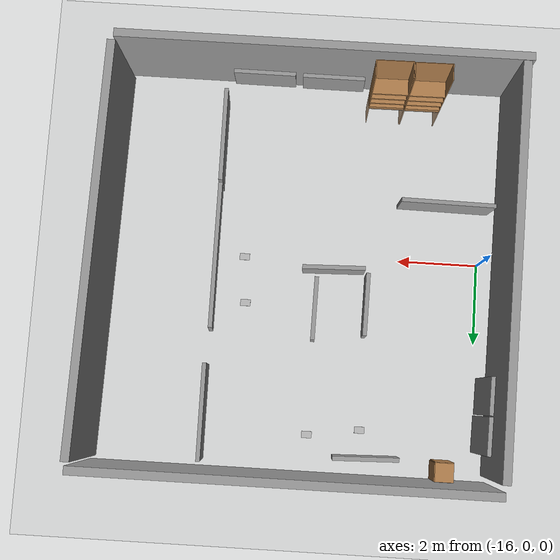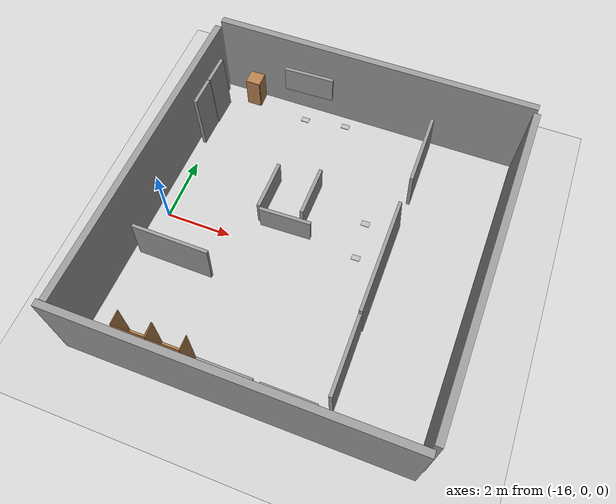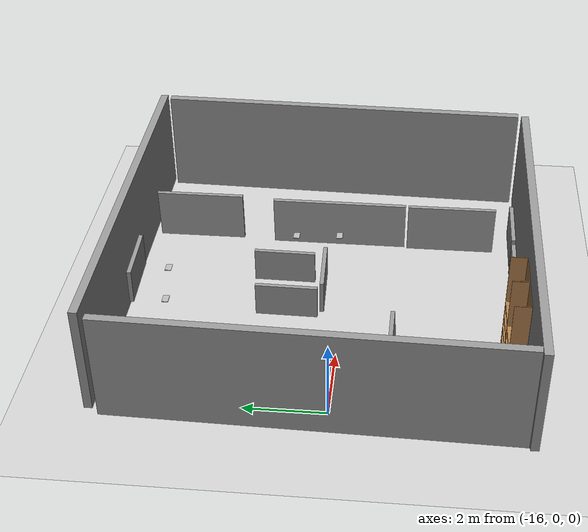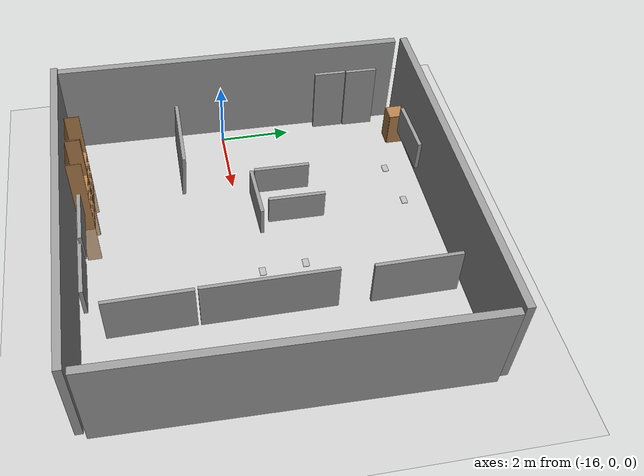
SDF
<sdf version="1.6">
 <world name="default">
  <light name="sun" type="directional">
   <pose>0 0 10 0 -0 0</pose>
   <diffuse>0.8 0.8 0.8 1</diffuse>
   <specular>0.2 0.2 0.2 1</specular>
   <attenuation>
    <range>1000</range>
    <constant>0.9</constant>
    <linear>0.01</linear>
    <quadratic>0.001</quadratic>
   </attenuation>
   <direction>-0.5 0.1 -0.9</direction>
  </light>
  <model name="ground_plane">
   <static>1</static>
   <link name="link">
    <collision name="collision">
     <geometry><plane><normal>0 0 1</normal><size>100 100</size></plane></geometry>
     <surface><friction><ode><mu>100</mu><mu2>50</mu2></ode></friction></surface>
    </collision>
    <visual name="visual">
     <cast_shadows>0</cast_shadows>
     <geometry><plane><normal>0 0 1</normal><size>100 100</size></plane></geometry>
     <material>
      <script><uri>file://media/materials/scripts/gazebo.material</uri><name>Gazebo/Grey</name></script>
     </material>
    </visual>
   </link>
  </model>
  <gravity>0 0 0</gravity>
  <magnetic_field>6e-06 2.3e-05 -4.2e-05</magnetic_field>
  <atmosphere type="adiabatic"/>
  <physics name="default_physics" default="0" type="ode">
   <max_step_size>0.001</max_step_size>
   <real_time_factor>1</real_time_factor>
   <real_time_update_rate>1000</real_time_update_rate>
  </physics>
  <scene><ambient>0.4 0.4 0.4 1</ambient><background>0.7 0.7 0.7 1</background><shadows>1</shadows></scene>
  <audio><device>default</device></audio>
  <spherical_coordinates>
   <surface_model>EARTH_WGS84</surface_model>
   <latitude_deg>0</latitude_deg>
   <longitude_deg>0</longitude_deg>
   <elevation>0</elevation>
   <heading_deg>0</heading_deg>
  </spherical_coordinates>
  <model name="grey_wall_clone">
   <link name="link">
    <pose>1.40413 -0.11801 1.4 0 -0 0</pose>
    <inertial>
     <mass>1.14359</mass>
     <inertia><ixx>0.750957</ixx><ixy>0</ixy><ixz>0</ixz><iyy>9.7518</iyy><iyz>0</iyz><izz>9.00846</izz></inertia>
    </inertial>
    <visual name="visual">
     <cast_shadows>0</cast_shadows>
     <geometry><box><size>9.72051 0.2 2.8</size></box></geometry>
     <material>
      <script>
       <uri>model://grey_wall/materials/scripts</uri>
       <uri>model://grey_wall/materials/textures</uri>
       <name>vrc/grey_wall</name>
      </script>
      <shader type="vertex"><normal_map>__default__</normal_map></shader>
      <ambient>1 1 1 1</ambient>
      <diffuse>1 1 1 1</diffuse>
      <specular>0 0 0 1</specular>
      <emissive>0 0 0 1</emissive>
     </material>
    </visual>
    <collision name="collision">
     <geometry><box><size>9.72051 0.2 2.8</size></box></geometry>
     <surface>
      <friction>
       <ode><mu>1</mu><mu2>1</mu2><fdir1>0 0 0</fdir1><slip1>0</slip1><slip2>0</slip2></ode>
       <torsional>
        <coefficient>1</coefficient>
        <patch_radius>0</patch_radius>
        <surface_radius>0</surface_radius>
        <use_patch_radius>1</use_patch_radius>
        <ode><slip>0</slip></ode>
       </torsional>
      </friction>
      <bounce><restitution_coefficient>0</restitution_coefficient><threshold>1e+06</threshold></bounce>
      <contact>
       <collide_without_contact>0</collide_without_contact>
       <collide_without_contact_bitmask>1</collide_without_contact_bitmask>
       <collide_bitmask>1</collide_bitmask>
       <ode>
        <soft_cfm>0</soft_cfm>
        <soft_erp>0.2</soft_erp>
        <kp>1e+13</kp>
        <kd>1</kd>
        <max_vel>0.01</max_vel>
        <min_depth>0</min_depth>
       </ode>
       <bullet>
        <split_impulse>1</split_impulse>
        <split_impulse_penetration_threshold>-0.01</split_impulse_penetration_threshold>
        <soft_cfm>0</soft_cfm>
        <soft_erp>0.2</soft_erp>
        <kp>1e+13</kp>
        <kd>1</kd>
       </bullet>
      </contact>
     </surface>
    </collision>
   </link>
   <static>1</static>
   <pose>-12.907 5.58737 0.05743 0 -0 0</pose>
  </model>
  <model name="grey_wall_clone_clone_0">
   <link name="link">
    <pose>1.17776 -0.11801 1.4 0 -0 0</pose>
    <inertial>
     <mass>1.16346</mass>
     <inertia><ixx>0.764005</ixx><ixy>0</ixy><ixz>0</ixz><iyy>10.2423</iyy><iyz>0</iyz><izz>9.48609</izz></inertia>
    </inertial>
    <visual name="visual">
     <cast_shadows>0</cast_shadows>
     <geometry><box><size>9.8894 0.2 2.8</size></box></geometry>
     <material>
      <script>
       <uri>model://grey_wall/materials/scripts</uri>
       <uri>model://grey_wall/materials/textures</uri>
       <name>vrc/grey_wall</name>
      </script>
      <shader type="vertex"><normal_map>__default__</normal_map></shader>
      <ambient>1 1 1 1</ambient>
      <diffuse>1 1 1 1</diffuse>
      <specular>0 0 0 1</specular>
      <emissive>0 0 0 1</emissive>
     </material>
    </visual>
    <collision name="collision">
     <geometry><box><size>9.8894 0.2 2.8</size></box></geometry>
     <surface>
      <friction>
       <ode><mu>1</mu><mu2>1</mu2><fdir1>0 0 0</fdir1><slip1>0</slip1><slip2>0</slip2></ode>
       <torsional>
        <coefficient>1</coefficient>
        <patch_radius>0</patch_radius>
        <surface_radius>0</surface_radius>
        <use_patch_radius>1</use_patch_radius>
        <ode><slip>0</slip></ode>
       </torsional>
      </friction>
      <bounce><restitution_coefficient>0</restitution_coefficient><threshold>1e+06</threshold></bounce>
      <contact>
       <collide_without_contact>0</collide_without_contact>
       <collide_without_contact_bitmask>1</collide_without_contact_bitmask>
       <collide_bitmask>1</collide_bitmask>
       <ode>
        <soft_cfm>0</soft_cfm>
        <soft_erp>0.2</soft_erp>
        <kp>1e+13</kp>
        <kd>1</kd>
        <max_vel>0.01</max_vel>
        <min_depth>0</min_depth>
       </ode>
       <bullet>
        <split_impulse>1</split_impulse>
        <split_impulse_penetration_threshold>-0.01</split_impulse_penetration_threshold>
        <soft_cfm>0</soft_cfm>
        <soft_erp>0.2</soft_erp>
        <kp>1e+13</kp>
        <kd>1</kd>
       </bullet>
      </contact>
     </surface>
    </collision>
   </link>
   <static>1</static>
   <pose>-12.9856 -4.50194 0 0 -0 0</pose>
  </model>
  <model name="grey_wall_clone_clone">
   <link name="link">
    <pose>0.291975 -0.11801 1.4 0 -0 0</pose>
    <inertial>
     <mass>1.14525</mass>
     <inertia><ixx>0.752049</ixx><ixy>0</ixy><ixz>0</ixz><iyy>9.79222</iyy><iyz>0</iyz><izz>9.04781</izz></inertia>
    </inertial>
    <visual name="visual">
     <cast_shadows>0</cast_shadows>
     <geometry><box><size>9.73464 0.2 2.8</size></box></geometry>
     <material>
      <script>
       <uri>model://grey_wall/materials/scripts</uri>
       <uri>model://grey_wall/materials/textures</uri>
       <name>vrc/grey_wall</name>
      </script>
      <shader type="vertex"><normal_map>__default__</normal_map></shader>
      <ambient>1 1 1 1</ambient>
      <diffuse>1 1 1 1</diffuse>
      <specular>0 0 0 1</specular>
      <emissive>0 0 0 1</emissive>
     </material>
    </visual>
    <collision name="collision">
     <geometry><box><size>9.73464 0.2 2.8</size></box></geometry>
     <surface>
      <friction>
       <ode><mu>1</mu><mu2>1</mu2><fdir1>0 0 0</fdir1><slip1>0</slip1><slip2>0</slip2></ode>
       <torsional>
        <coefficient>1</coefficient>
        <patch_radius>0</patch_radius>
        <surface_radius>0</surface_radius>
        <use_patch_radius>1</use_patch_radius>
        <ode><slip>0</slip></ode>
       </torsional>
      </friction>
      <bounce><restitution_coefficient>0</restitution_coefficient><threshold>1e+06</threshold></bounce>
      <contact>
       <collide_without_contact>0</collide_without_contact>
       <collide_without_contact_bitmask>1</collide_without_contact_bitmask>
       <collide_bitmask>1</collide_bitmask>
       <ode>
        <soft_cfm>0</soft_cfm>
        <soft_erp>0.2</soft_erp>
        <kp>1e+13</kp>
        <kd>1</kd>
        <max_vel>0.01</max_vel>
        <min_depth>0</min_depth>
       </ode>
       <bullet>
        <split_impulse>1</split_impulse>
        <split_impulse_penetration_threshold>-0.01</split_impulse_penetration_threshold>
        <soft_cfm>0</soft_cfm>
        <soft_erp>0.2</soft_erp>
        <kp>1e+13</kp>
        <kd>1</kd>
       </bullet>
      </contact>
     </surface>
    </collision>
   </link>
   <static>1</static>
   <pose>-16.6059 0.064123 0 0 -0 1.55187</pose>
  </model>
  <model name="unit_box_clone_0_clone_clone_0">
   <link name="link">
    <inertial>
     <mass>0.724105</mass>
     <inertia>
      <ixx>0.0453015</ixx>
      <ixy>0</ixy>
      <ixz>0</ixz>
      <iyy>0.183143</iyy>
      <iyz>0</iyz>
      <izz>0.139048</izz>
     </inertia>
    </inertial>
    <pose>0.262043 -0.534144 0 0 -0 1.59038</pose>
    <visual name="visual">
     <geometry><box><size>1.5147 0.1 0.860665</size></box></geometry>
     <material>
      <script><name>Gazebo/Grey</name><uri>file://media/materials/scripts/gazebo.material</uri></script>
      <shader type="vertex"><normal_map>__default__</normal_map></shader>
      <ambient>0 0 0 1</ambient>
      <diffuse>0 0 0 1</diffuse>
      <specular>0.01 0.01 0.01 1</specular>
      <emissive>0 0 0 1</emissive>
     </material>
    </visual>
    <collision name="collision">
     <geometry><box><size>1.5147 0.1 0.860665</size></box></geometry>
     <surface>
      <friction>
       <ode><mu>1</mu><mu2>1</mu2><fdir1>0 0 0</fdir1><slip1>0</slip1><slip2>0</slip2></ode>
       <torsional>
        <coefficient>1</coefficient>
        <patch_radius>0</patch_radius>
        <surface_radius>0</surface_radius>
        <use_patch_radius>1</use_patch_radius>
        <ode><slip>0</slip></ode>
       </torsional>
      </friction>
      <bounce><restitution_coefficient>0</restitution_coefficient><threshold>1e+06</threshold></bounce>
      <contact>
       <collide_without_contact>0</collide_without_contact>
       <collide_without_contact_bitmask>1</collide_without_contact_bitmask>
       <collide_bitmask>1</collide_bitmask>
       <ode>
        <soft_cfm>0</soft_cfm>
        <soft_erp>0.2</soft_erp>
        <kp>1e+13</kp>
        <kd>1</kd>
        <max_vel>0.01</max_vel>
        <min_depth>0</min_depth>
       </ode>
       <bullet>
        <split_impulse>1</split_impulse>
        <split_impulse_penetration_threshold>-0.01</split_impulse_penetration_threshold>
        <soft_cfm>0</soft_cfm>
        <soft_erp>0.2</soft_erp>
        <kp>1e+13</kp>
        <kd>1</kd>
       </bullet>
      </contact>
     </surface>
    </collision>
   </link>
   <static>1</static>
   <pose>-9.85653 -3.99567 1.22283 0.000117 -0.002185 -1.59437</pose>
  </model>
  <model name="unit_box_clone_0_clone_clone_0_clone_clone">
   <link name="link">
    <inertial>
     <mass>0.724105</mass>
     <inertia>
      <ixx>0.0453015</ixx>
      <ixy>0</ixy>
      <ixz>0</ixz>
      <iyy>0.183143</iyy>
      <iyz>0</iyz>
      <izz>0.139048</izz>
     </inertia>
    </inertial>
    <pose>0.262043 -0.534144 0 0 -0 1.59038</pose>
    <visual name="visual">
     <geometry><box><size>1.5147 0.1 0.860665</size></box></geometry>
     <material>
      <script><name>Gazebo/Grey</name><uri>file://media/materials/scripts/gazebo.material</uri></script>
      <shader type="vertex"><normal_map>__default__</normal_map></shader>
      <ambient>0 0 0 1</ambient>
      <diffuse>0 0 0 1</diffuse>
      <specular>0.01 0.01 0.01 1</specular>
      <emissive>0 0 0 1</emissive>
     </material>
    </visual>
    <collision name="collision">
     <geometry><box><size>1.5147 0.1 0.860665</size></box></geometry>
     <surface>
      <friction>
       <ode><mu>1</mu><mu2>1</mu2><fdir1>0 0 0</fdir1><slip1>0</slip1><slip2>0</slip2></ode>
       <torsional>
        <coefficient>1</coefficient>
        <patch_radius>0</patch_radius>
        <surface_radius>0</surface_radius>
        <use_patch_radius>1</use_patch_radius>
        <ode><slip>0</slip></ode>
       </torsional>
      </friction>
      <bounce><restitution_coefficient>0</restitution_coefficient><threshold>1e+06</threshold></bounce>
      <contact>
       <collide_without_contact>0</collide_without_contact>
       <collide_without_contact_bitmask>1</collide_without_contact_bitmask>
       <collide_bitmask>1</collide_bitmask>
       <ode>
        <soft_cfm>0</soft_cfm>
        <soft_erp>0.2</soft_erp>
        <kp>1e+13</kp>
        <kd>1</kd>
        <max_vel>0.01</max_vel>
        <min_depth>0</min_depth>
       </ode>
       <bullet>
        <split_impulse>1</split_impulse>
        <split_impulse_penetration_threshold>-0.01</split_impulse_penetration_threshold>
        <soft_cfm>0</soft_cfm>
        <soft_erp>0.2</soft_erp>
        <kp>1e+13</kp>
        <kd>1</kd>
       </bullet>
      </contact>
     </surface>
    </collision>
   </link>
   <static>1</static>
   <pose>-13.4302 1.81234 0.970187 -3e-05 0.001515 -0.03305</pose>
  </model>
  <model name="unit_box_clone_0_clone_clone_0_clone_clone_0">
   <link name="link">
    <inertial>
     <mass>0.724105</mass>
     <inertia>
      <ixx>0.0453015</ixx>
      <ixy>0</ixy>
      <ixz>0</ixz>
      <iyy>0.183143</iyy>
      <iyz>0</iyz>
      <izz>0.139048</izz>
     </inertia>
    </inertial>
    <pose>0.262043 -0.534144 0 0 -0 1.59038</pose>
    <visual name="visual">
     <geometry><box><size>1.5147 0.1 0.860665</size></box></geometry>
     <material>
      <script><name>Gazebo/Grey</name><uri>file://media/materials/scripts/gazebo.material</uri></script>
      <shader type="vertex"><normal_map>__default__</normal_map></shader>
      <ambient>0 0 0 1</ambient>
      <diffuse>0 0 0 1</diffuse>
      <specular>0.01 0.01 0.01 1</specular>
      <emissive>0 0 0 1</emissive>
     </material>
    </visual>
    <collision name="collision">
     <geometry><box><size>1.5147 0.1 0.860665</size></box></geometry>
     <surface>
      <friction>
       <ode><mu>1</mu><mu2>1</mu2><fdir1>0 0 0</fdir1><slip1>0</slip1><slip2>0</slip2></ode>
       <torsional>
        <coefficient>1</coefficient>
        <patch_radius>0</patch_radius>
        <surface_radius>0</surface_radius>
        <use_patch_radius>1</use_patch_radius>
        <ode><slip>0</slip></ode>
       </torsional>
      </friction>
      <bounce><restitution_coefficient>0</restitution_coefficient><threshold>1e+06</threshold></bounce>
      <contact>
       <collide_without_contact>0</collide_without_contact>
       <collide_without_contact_bitmask>1</collide_without_contact_bitmask>
       <collide_bitmask>1</collide_bitmask>
       <ode>
        <soft_cfm>0</soft_cfm>
        <soft_erp>0.2</soft_erp>
        <kp>1e+13</kp>
        <kd>1</kd>
        <max_vel>0.01</max_vel>
        <min_depth>0</min_depth>
       </ode>
       <bullet>
        <split_impulse>1</split_impulse>
        <split_impulse_penetration_threshold>-0.01</split_impulse_penetration_threshold>
        <soft_cfm>0</soft_cfm>
        <soft_erp>0.2</soft_erp>
        <kp>1e+13</kp>
        <kd>1</kd>
       </bullet>
      </contact>
     </surface>
    </collision>
   </link>
   <static>1</static>
   <pose>-11.8227 0.703821 1.03594 -1e-06 3.4e-05 -1.56064</pose>
  </model>
  <model name="unit_box_clone_0_clone_clone_0_clone_clone_0_clone">
   <link name="link">
    <inertial>
     <mass>0.724105</mass>
     <inertia>
      <ixx>0.0453015</ixx>
      <ixy>0</ixy>
      <ixz>0</ixz>
      <iyy>0.183143</iyy>
      <iyz>0</iyz>
      <izz>0.139048</izz>
     </inertia>
    </inertial>
    <pose>0.262043 -0.534144 0 0 -0 1.59038</pose>
    <visual name="visual">
     <geometry><box><size>1.5147 0.1 0.860665</size></box></geometry>
     <material>
      <script><name>Gazebo/Grey</name><uri>file://media/materials/scripts/gazebo.material</uri></script>
      <shader type="vertex"><normal_map>__default__</normal_map></shader>
      <ambient>0 0 0 1</ambient>
      <diffuse>0 0 0 1</diffuse>
      <specular>0.01 0.01 0.01 1</specular>
      <emissive>0 0 0 1</emissive>
     </material>
    </visual>
    <collision name="collision">
     <geometry><box><size>1.5147 0.1 0.860665</size></box></geometry>
     <surface>
      <friction>
       <ode><mu>1</mu><mu2>1</mu2><fdir1>0 0 0</fdir1><slip1>0</slip1><slip2>0</slip2></ode>
       <torsional>
        <coefficient>1</coefficient>
        <patch_radius>0</patch_radius>
        <surface_radius>0</surface_radius>
        <use_patch_radius>1</use_patch_radius>
        <ode><slip>0</slip></ode>
       </torsional>
      </friction>
      <bounce><restitution_coefficient>0</restitution_coefficient><threshold>1e+06</threshold></bounce>
      <contact>
       <collide_without_contact>0</collide_without_contact>
       <collide_without_contact_bitmask>1</collide_without_contact_bitmask>
       <collide_bitmask>1</collide_bitmask>
       <ode>
        <soft_cfm>0</soft_cfm>
        <soft_erp>0.2</soft_erp>
        <kp>1e+13</kp>
        <kd>1</kd>
        <max_vel>0.01</max_vel>
        <min_depth>0</min_depth>
       </ode>
       <bullet>
        <split_impulse>1</split_impulse>
        <split_impulse_penetration_threshold>-0.01</split_impulse_penetration_threshold>
        <soft_cfm>0</soft_cfm>
        <soft_erp>0.2</soft_erp>
        <kp>1e+13</kp>
        <kd>1</kd>
       </bullet>
      </contact>
     </surface>
    </collision>
   </link>
   <static>1</static>
   <pose>-12.7715 5.13782 1.80351 -0.000124 0.006448 -1.56064</pose>
  </model>
  <model name="unit_box_clone_clone">
   <link name="link">
    <inertial>
     <mass>1</mass>
     <inertia>
      <ixx>0.166667</ixx>
      <ixy>0</ixy>
      <ixz>0</ixz>
      <iyy>0.166667</iyy>
      <iyz>0</iyz>
      <izz>0.166667</izz>
     </inertia>
    </inertial>
    <pose>0 0 0 0 -0 1.59038</pose>
    <visual name="visual">
     <geometry><box><size>0.9 0.1 2</size></box></geometry>
     <material>
      <script><name>Gazebo/Grey</name><uri>file://media/materials/scripts/gazebo.material</uri></script>
      <shader type="vertex"><normal_map>__default__</normal_map></shader>
      <ambient>0.3 0.3 0.3 1</ambient>
      <diffuse>0.7 0.7 0.7 1</diffuse>
      <specular>0.01 0.01 0.01 1</specular>
      <emissive>0 0 0 1</emissive>
     </material>
    </visual>
    <collision name="collision">
     <geometry><box><size>0.9 0.1 2</size></box></geometry>
     <surface>
      <friction>
       <ode><mu>1</mu><mu2>1</mu2><fdir1>0 0 0</fdir1><slip1>0</slip1><slip2>0</slip2></ode>
       <torsional>
        <coefficient>1</coefficient>
        <patch_radius>0</patch_radius>
        <surface_radius>0</surface_radius>
        <use_patch_radius>1</use_patch_radius>
        <ode><slip>0</slip></ode>
       </torsional>
      </friction>
      <bounce><restitution_coefficient>0</restitution_coefficient><threshold>1e+06</threshold></bounce>
      <contact>
       <collide_without_contact>0</collide_without_contact>
       <collide_without_contact_bitmask>1</collide_without_contact_bitmask>
       <collide_bitmask>1</collide_bitmask>
       <ode>
        <soft_cfm>0</soft_cfm>
        <soft_erp>0.2</soft_erp>
        <kp>1e+13</kp>
        <kd>1</kd>
        <max_vel>0.01</max_vel>
        <min_depth>0</min_depth>
       </ode>
       <bullet>
        <split_impulse>1</split_impulse>
        <split_impulse_penetration_threshold>-0.01</split_impulse_penetration_threshold>
        <soft_cfm>0</soft_cfm>
        <soft_erp>0.2</soft_erp>
        <kp>1e+13</kp>
        <kd>1</kd>
       </bullet>
      </contact>
     </surface>
    </collision>
   </link>
   <static>1</static>
   <pose>-16.1079 4.21079 1.01917 0.005165 -0.025451 -0.048475</pose>
  </model>
  <model name="unit_box_clone_0_clone_clone_clone_0_clone_clone">
   <link name="link">
    <inertial>
     <mass>1.76092</mass>
     <inertia><ixx>0.27833</ixx><ixy>0</ixy><ixz>0</ixz><iyy>1.05856</iyy><iyz>0</iyz><izz>0.783161</izz></inertia>
    </inertial>
    <pose>0.262043 -0.534144 -0 0 -0 1.59038</pose>
    <visual name="visual">
     <geometry><box><size>2.30802 0.1 1.37358</size></box></geometry>
     <material>
      <script><name>Gazebo/Grey</name><uri>file://media/materials/scripts/gazebo.material</uri></script>
      <shader type="vertex"><normal_map>__default__</normal_map></shader>
      <ambient>0.8 0.8 0.8 1</ambient>
      <diffuse>0 0 0 1</diffuse>
      <specular>0.01 0.01 0.01 1</specular>
      <emissive>0 0 0 1</emissive>
     </material>
    </visual>
    <collision name="collision">
     <geometry><box><size>2.30802 0.1 1.37358</size></box></geometry>
     <surface>
      <friction>
       <ode><mu>1</mu><mu2>1</mu2><fdir1>0 0 0</fdir1><slip1>0</slip1><slip2>0</slip2></ode>
       <torsional>
        <coefficient>1</coefficient>
        <patch_radius>0</patch_radius>
        <surface_radius>0</surface_radius>
        <use_patch_radius>1</use_patch_radius>
        <ode><slip>0</slip></ode>
       </torsional>
      </friction>
      <bounce><restitution_coefficient>0</restitution_coefficient><threshold>1e+06</threshold></bounce>
      <contact>
       <collide_without_contact>0</collide_without_contact>
       <collide_without_contact_bitmask>1</collide_without_contact_bitmask>
       <collide_bitmask>1</collide_bitmask>
       <ode>
        <soft_cfm>0</soft_cfm>
        <soft_erp>0.2</soft_erp>
        <kp>1e+13</kp>
        <kd>1</kd>
        <max_vel>0.01</max_vel>
        <min_depth>0</min_depth>
       </ode>
       <bullet>
        <split_impulse>1</split_impulse>
        <split_impulse_penetration_threshold>-0.01</split_impulse_penetration_threshold>
        <soft_cfm>0</soft_cfm>
        <soft_erp>0.2</soft_erp>
        <kp>1e+13</kp>
        <kd>1</kd>
       </bullet>
      </contact>
     </surface>
    </collision>
   </link>
   <static>1</static>
   <pose>-9.68625 -2.18324 0.688928 0.000802 -0.047021 -0.014366</pose>
  </model>
  <model name="unit_box_clone_0_clone_clone_clone_0_clone_clone_0">
   <link name="link">
    <inertial>
     <mass>1.76092</mass>
     <inertia><ixx>0.27833</ixx><ixy>0</ixy><ixz>0</ixz><iyy>1.05856</iyy><iyz>0</iyz><izz>0.783161</izz></inertia>
    </inertial>
    <pose>0.262043 -0.534144 -0 0 -0 1.59038</pose>
    <visual name="visual">
     <geometry><box><size>2.30802 0.1 1.37358</size></box></geometry>
     <material>
      <script><name>Gazebo/Grey</name><uri>file://media/materials/scripts/gazebo.material</uri></script>
      <shader type="vertex"><normal_map>__default__</normal_map></shader>
      <ambient>0.8 0.8 0.8 1</ambient>
      <diffuse>0 0 0 1</diffuse>
      <specular>0.01 0.01 0.01 1</specular>
      <emissive>0 0 0 1</emissive>
     </material>
    </visual>
    <collision name="collision">
     <geometry><box><size>2.30802 0.1 1.37358</size></box></geometry>
     <surface>
      <friction>
       <ode><mu>1</mu><mu2>1</mu2><fdir1>0 0 0</fdir1><slip1>0</slip1><slip2>0</slip2></ode>
       <torsional>
        <coefficient>1</coefficient>
        <patch_radius>0</patch_radius>
        <surface_radius>0</surface_radius>
        <use_patch_radius>1</use_patch_radius>
        <ode><slip>0</slip></ode>
       </torsional>
      </friction>
      <bounce><restitution_coefficient>0</restitution_coefficient><threshold>1e+06</threshold></bounce>
      <contact>
       <collide_without_contact>0</collide_without_contact>
       <collide_without_contact_bitmask>1</collide_without_contact_bitmask>
       <collide_bitmask>1</collide_bitmask>
       <ode>
        <soft_cfm>0</soft_cfm>
        <soft_erp>0.2</soft_erp>
        <kp>1e+13</kp>
        <kd>1</kd>
        <max_vel>0.01</max_vel>
        <min_depth>0</min_depth>
       </ode>
       <bullet>
        <split_impulse>1</split_impulse>
        <split_impulse_penetration_threshold>-0.01</split_impulse_penetration_threshold>
        <soft_cfm>0</soft_cfm>
        <soft_erp>0.2</soft_erp>
        <kp>1e+13</kp>
        <kd>1</kd>
       </bullet>
      </contact>
     </surface>
    </collision>
   </link>
   <static>1</static>
   <pose>-9.63931 4.58608 0.725129 0.000802 -0.04702 -0.014366</pose>
  </model>
  <model name="bookshelf_0">
   <link name="link">
    <inertial>
     <mass>3.22474</mass>
     <inertia>
      <ixx>0.0441157</ixx>
      <ixy>0</ixy>
      <ixz>0</ixz>
      <iyy>0.209222</iyy>
      <iyz>0</iyz>
      <izz>0.2511</izz>
     </inertia>
    </inertial>
    <pose>0 0 0 0 0 -3.13313</pose>
    <visual name="visual1">
     <pose>0 0.005 0.6 0 -0 0</pose>
     <geometry><box><size>0.9 0.01 3.8752</size></box></geometry>
     <material>
      <script><uri>file://media/materials/scripts/gazebo.material</uri><name>Gazebo/Wood</name></script>
     </material>
    </visual>
    <visual name="visual2">
     <pose>0.45 -0.195 0.6 0 -0 0</pose>
     <geometry><box><size>0.02 0.4 3.8752</size></box></geometry>
     <material>
      <script><uri>file://media/materials/scripts/gazebo.material</uri><name>Gazebo/Wood</name></script>
     </material>
    </visual>
    <visual name="visual3">
     <pose>-0.45 -0.195 0.6 0 -0 0</pose>
     <geometry><box><size>0.02 0.4 3.8752</size></box></geometry>
     <material>
      <script><uri>file://media/materials/scripts/gazebo.material</uri><name>Gazebo/Wood</name></script>
     </material>
    </visual>
    <visual name="visual4">
     <pose>0 -0.195 0.03 0 -0 0</pose>
     <geometry><box><size>0.88 0.4 0.193307</size></box></geometry>
     <material>
      <script><uri>file://media/materials/scripts/gazebo.material</uri><name>Gazebo/Wood</name></script>
     </material>
    </visual>
    <visual name="visual5">
     <pose>0 -0.195 1.19 0 -0 0</pose>
     <geometry><box><size>0.88 0.4 0.064536</size></box></geometry>
     <material>
      <script><uri>file://media/materials/scripts/gazebo.material</uri><name>Gazebo/Wood</name></script>
     </material>
    </visual>
    <visual name="visual6">
     <pose>0 -0.195 0.43 0 -0 0</pose>
     <geometry><box><size>0.88 0.4 0.064536</size></box></geometry>
     <material>
      <script><uri>file://media/materials/scripts/gazebo.material</uri><name>Gazebo/Wood</name></script>
     </material>
    </visual>
    <visual name="visual7">
     <pose>0 -0.195 0.8 0 -0 0</pose>
     <geometry><box><size>0.88 0.4 0.064536</size></box></geometry>
     <material>
      <script><uri>file://media/materials/scripts/gazebo.material</uri><name>Gazebo/Wood</name></script>
     </material>
    </visual>
    <collision name="back">
     <pose>0 0.005 0.6 0 -0 0</pose>
     <geometry><box><size>0.9 0.01 3.8752</size></box></geometry>
     <surface>
      <friction>
       <ode><mu>1</mu><mu2>1</mu2><fdir1>0 0 0</fdir1><slip1>0</slip1><slip2>0</slip2></ode>
       <torsional>
        <coefficient>1</coefficient>
        <patch_radius>0</patch_radius>
        <surface_radius>0</surface_radius>
        <use_patch_radius>1</use_patch_radius>
        <ode><slip>0</slip></ode>
       </torsional>
      </friction>
      <bounce><restitution_coefficient>0</restitution_coefficient><threshold>1e+06</threshold></bounce>
      <contact>
       <collide_without_contact>0</collide_without_contact>
       <collide_without_contact_bitmask>1</collide_without_contact_bitmask>
       <collide_bitmask>1</collide_bitmask>
       <ode>
        <soft_cfm>0</soft_cfm>
        <soft_erp>0.2</soft_erp>
        <kp>1e+13</kp>
        <kd>1</kd>
        <max_vel>0.01</max_vel>
        <min_depth>0</min_depth>
       </ode>
       <bullet>
        <split_impulse>1</split_impulse>
        <split_impulse_penetration_threshold>-0.01</split_impulse_penetration_threshold>
        <soft_cfm>0</soft_cfm>
        <soft_erp>0.2</soft_erp>
        <kp>1e+13</kp>
        <kd>1</kd>
       </bullet>
      </contact>
     </surface>
    </collision>
    <collision name="left_side">
     <pose>0.45 -0.195 0.6 0 -0 0</pose>
     <geometry><box><size>0.02 0.4 3.8752</size></box></geometry>
     <surface>
      <friction>
       <ode><mu>1</mu><mu2>1</mu2><fdir1>0 0 0</fdir1><slip1>0</slip1><slip2>0</slip2></ode>
       <torsional>
        <coefficient>1</coefficient>
        <patch_radius>0</patch_radius>
        <surface_radius>0</surface_radius>
        <use_patch_radius>1</use_patch_radius>
        <ode><slip>0</slip></ode>
       </torsional>
      </friction>
      <bounce><restitution_coefficient>0</restitution_coefficient><threshold>1e+06</threshold></bounce>
      <contact>
       <collide_without_contact>0</collide_without_contact>
       <collide_without_contact_bitmask>1</collide_without_contact_bitmask>
       <collide_bitmask>1</collide_bitmask>
       <ode>
        <soft_cfm>0</soft_cfm>
        <soft_erp>0.2</soft_erp>
        <kp>1e+13</kp>
        <kd>1</kd>
        <max_vel>0.01</max_vel>
        <min_depth>0</min_depth>
       </ode>
       <bullet>
        <split_impulse>1</split_impulse>
        <split_impulse_penetration_threshold>-0.01</split_impulse_penetration_threshold>
        <soft_cfm>0</soft_cfm>
        <soft_erp>0.2</soft_erp>
        <kp>1e+13</kp>
        <kd>1</kd>
       </bullet>
      </contact>
     </surface>
    </collision>
    <collision name="right_side">
     <pose>-0.45 -0.195 0.6 0 -0 0</pose>
     <geometry><box><size>0.02 0.4 3.8752</size></box></geometry>
     <surface>
      <friction>
       <ode><mu>1</mu><mu2>1</mu2><fdir1>0 0 0</fdir1><slip1>0</slip1><slip2>0</slip2></ode>
       <torsional>
        <coefficient>1</coefficient>
        <patch_radius>0</patch_radius>
        <surface_radius>0</surface_radius>
        <use_patch_radius>1</use_patch_radius>
        <ode><slip>0</slip></ode>
       </torsional>
      </friction>
      <bounce><restitution_coefficient>0</restitution_coefficient><threshold>1e+06</threshold></bounce>
      <contact>
       <collide_without_contact>0</collide_without_contact>
       <collide_without_contact_bitmask>1</collide_without_contact_bitmask>
       <collide_bitmask>1</collide_bitmask>
       <ode>
        <soft_cfm>0</soft_cfm>
        <soft_erp>0.2</soft_erp>
        <kp>1e+13</kp>
        <kd>1</kd>
        <max_vel>0.01</max_vel>
        <min_depth>0</min_depth>
       </ode>
       <bullet>
        <split_impulse>1</split_impulse>
        <split_impulse_penetration_threshold>-0.01</split_impulse_penetration_threshold>
        <soft_cfm>0</soft_cfm>
        <soft_erp>0.2</soft_erp>
        <kp>1e+13</kp>
        <kd>1</kd>
       </bullet>
      </contact>
     </surface>
    </collision>
    <collision name="bottom">
     <pose>0 -0.195 0.03 0 -0 0</pose>
     <geometry><box><size>0.88 0.4 0.193307</size></box></geometry>
     <surface>
      <friction>
       <ode><mu>1</mu><mu2>1</mu2><fdir1>0 0 0</fdir1><slip1>0</slip1><slip2>0</slip2></ode>
       <torsional>
        <coefficient>1</coefficient>
        <patch_radius>0</patch_radius>
        <surface_radius>0</surface_radius>
        <use_patch_radius>1</use_patch_radius>
        <ode><slip>0</slip></ode>
       </torsional>
      </friction>
      <bounce><restitution_coefficient>0</restitution_coefficient><threshold>1e+06</threshold></bounce>
      <contact>
       <collide_without_contact>0</collide_without_contact>
       <collide_without_contact_bitmask>1</collide_without_contact_bitmask>
       <collide_bitmask>1</collide_bitmask>
       <ode>
        <soft_cfm>0</soft_cfm>
        <soft_erp>0.2</soft_erp>
        <kp>1e+13</kp>
        <kd>1</kd>
        <max_vel>0.01</max_vel>
        <min_depth>0</min_depth>
       </ode>
       <bullet>
        <split_impulse>1</split_impulse>
        <split_impulse_penetration_threshold>-0.01</split_impulse_penetration_threshold>
        <soft_cfm>0</soft_cfm>
        <soft_erp>0.2</soft_erp>
        <kp>1e+13</kp>
        <kd>1</kd>
       </bullet>
      </contact>
     </surface>
    </collision>
    <collision name="top">
     <pose>0 -0.195 1.19 0 -0 0</pose>
     <geometry><box><size>0.88 0.4 0.064536</size></box></geometry>
     <surface>
      <friction>
       <ode><mu>1</mu><mu2>1</mu2><fdir1>0 0 0</fdir1><slip1>0</slip1><slip2>0</slip2></ode>
       <torsional>
        <coefficient>1</coefficient>
        <patch_radius>0</patch_radius>
        <surface_radius>0</surface_radius>
        <use_patch_radius>1</use_patch_radius>
        <ode><slip>0</slip></ode>
       </torsional>
      </friction>
      <bounce><restitution_coefficient>0</restitution_coefficient><threshold>1e+06</threshold></bounce>
      <contact>
       <collide_without_contact>0</collide_without_contact>
       <collide_without_contact_bitmask>1</collide_without_contact_bitmask>
       <collide_bitmask>1</collide_bitmask>
       <ode>
        <soft_cfm>0</soft_cfm>
        <soft_erp>0.2</soft_erp>
        <kp>1e+13</kp>
        <kd>1</kd>
        <max_vel>0.01</max_vel>
        <min_depth>0</min_depth>
       </ode>
       <bullet>
        <split_impulse>1</split_impulse>
        <split_impulse_penetration_threshold>-0.01</split_impulse_penetration_threshold>
        <soft_cfm>0</soft_cfm>
        <soft_erp>0.2</soft_erp>
        <kp>1e+13</kp>
        <kd>1</kd>
       </bullet>
      </contact>
     </surface>
    </collision>
    <collision name="low_shelf">
     <pose>0 -0.195 0.43 0 -0 0</pose>
     <geometry><box><size>0.88 0.4 0.064536</size></box></geometry>
     <surface>
      <friction>
       <ode><mu>1</mu><mu2>1</mu2><fdir1>0 0 0</fdir1><slip1>0</slip1><slip2>0</slip2></ode>
       <torsional>
        <coefficient>1</coefficient>
        <patch_radius>0</patch_radius>
        <surface_radius>0</surface_radius>
        <use_patch_radius>1</use_patch_radius>
        <ode><slip>0</slip></ode>
       </torsional>
      </friction>
      <bounce><restitution_coefficient>0</restitution_coefficient><threshold>1e+06</threshold></bounce>
      <contact>
       <collide_without_contact>0</collide_without_contact>
       <collide_without_contact_bitmask>1</collide_without_contact_bitmask>
       <collide_bitmask>1</collide_bitmask>
       <ode>
        <soft_cfm>0</soft_cfm>
        <soft_erp>0.2</soft_erp>
        <kp>1e+13</kp>
        <kd>1</kd>
        <max_vel>0.01</max_vel>
        <min_depth>0</min_depth>
       </ode>
       <bullet>
        <split_impulse>1</split_impulse>
        <split_impulse_penetration_threshold>-0.01</split_impulse_penetration_threshold>
        <soft_cfm>0</soft_cfm>
        <soft_erp>0.2</soft_erp>
        <kp>1e+13</kp>
        <kd>1</kd>
       </bullet>
      </contact>
     </surface>
    </collision>
    <collision name="high_shelf">
     <pose>0 -0.195 0.8 0 -0 0</pose>
     <geometry><box><size>0.88 0.4 0.064536</size></box></geometry>
     <surface>
      <friction>
       <ode><mu>1</mu><mu2>1</mu2><fdir1>0 0 0</fdir1><slip1>0</slip1><slip2>0</slip2></ode>
       <torsional>
        <coefficient>1</coefficient>
        <patch_radius>0</patch_radius>
        <surface_radius>0</surface_radius>
        <use_patch_radius>1</use_patch_radius>
        <ode><slip>0</slip></ode>
       </torsional>
      </friction>
      <bounce><restitution_coefficient>0</restitution_coefficient><threshold>1e+06</threshold></bounce>
      <contact>
       <collide_without_contact>0</collide_without_contact>
       <collide_without_contact_bitmask>1</collide_without_contact_bitmask>
       <collide_bitmask>1</collide_bitmask>
       <ode>
        <soft_cfm>0</soft_cfm>
        <soft_erp>0.2</soft_erp>
        <kp>1e+13</kp>
        <kd>1</kd>
        <max_vel>0.01</max_vel>
        <min_depth>0</min_depth>
       </ode>
       <bullet>
        <split_impulse>1</split_impulse>
        <split_impulse_penetration_threshold>-0.01</split_impulse_penetration_threshold>
        <soft_cfm>0</soft_cfm>
        <soft_erp>0.2</soft_erp>
        <kp>1e+13</kp>
        <kd>1</kd>
       </bullet>
      </contact>
     </surface>
    </collision>
   </link>
   <static>1</static>
   <pose>-13.5081 -4.40794 0 0 -0 0</pose>
  </model>
  <model name="bookshelf_0_clone">
   <link name="link">
    <inertial>
     <mass>3.22474</mass>
     <inertia>
      <ixx>0.0441157</ixx>
      <ixy>0</ixy>
      <ixz>0</ixz>
      <iyy>0.209222</iyy>
      <iyz>0</iyz>
      <izz>0.2511</izz>
     </inertia>
    </inertial>
    <pose>0 0 0 0 0 -3.13313</pose>
    <visual name="visual1">
     <pose>0 0.005 0.6 0 -0 0</pose>
     <geometry><box><size>0.9 0.01 3.8752</size></box></geometry>
     <material>
      <script><uri>file://media/materials/scripts/gazebo.material</uri><name>Gazebo/Wood</name></script>
     </material>
    </visual>
    <visual name="visual2">
     <pose>0.45 -0.195 0.6 0 -0 0</pose>
     <geometry><box><size>0.02 0.4 3.8752</size></box></geometry>
     <material>
      <script><uri>file://media/materials/scripts/gazebo.material</uri><name>Gazebo/Wood</name></script>
     </material>
    </visual>
    <visual name="visual3">
     <pose>-0.45 -0.195 0.6 0 -0 0</pose>
     <geometry><box><size>0.02 0.4 3.8752</size></box></geometry>
     <material>
      <script><uri>file://media/materials/scripts/gazebo.material</uri><name>Gazebo/Wood</name></script>
     </material>
    </visual>
    <visual name="visual4">
     <pose>0 -0.195 0.03 0 -0 0</pose>
     <geometry><box><size>0.88 0.4 0.193307</size></box></geometry>
     <material>
      <script><uri>file://media/materials/scripts/gazebo.material</uri><name>Gazebo/Wood</name></script>
     </material>
    </visual>
    <visual name="visual5">
     <pose>0 -0.195 1.19 0 -0 0</pose>
     <geometry><box><size>0.88 0.4 0.064536</size></box></geometry>
     <material>
      <script><uri>file://media/materials/scripts/gazebo.material</uri><name>Gazebo/Wood</name></script>
     </material>
    </visual>
    <visual name="visual6">
     <pose>0 -0.195 0.43 0 -0 0</pose>
     <geometry><box><size>0.88 0.4 0.064536</size></box></geometry>
     <material>
      <script><uri>file://media/materials/scripts/gazebo.material</uri><name>Gazebo/Wood</name></script>
     </material>
    </visual>
    <visual name="visual7">
     <pose>0 -0.195 0.8 0 -0 0</pose>
     <geometry><box><size>0.88 0.4 0.064536</size></box></geometry>
     <material>
      <script><uri>file://media/materials/scripts/gazebo.material</uri><name>Gazebo/Wood</name></script>
     </material>
    </visual>
    <collision name="back">
     <pose>0 0.005 0.6 0 -0 0</pose>
     <geometry><box><size>0.9 0.01 3.8752</size></box></geometry>
     <surface>
      <friction>
       <ode><mu>1</mu><mu2>1</mu2><fdir1>0 0 0</fdir1><slip1>0</slip1><slip2>0</slip2></ode>
       <torsional>
        <coefficient>1</coefficient>
        <patch_radius>0</patch_radius>
        <surface_radius>0</surface_radius>
        <use_patch_radius>1</use_patch_radius>
        <ode><slip>0</slip></ode>
       </torsional>
      </friction>
      <bounce><restitution_coefficient>0</restitution_coefficient><threshold>1e+06</threshold></bounce>
      <contact>
       <collide_without_contact>0</collide_without_contact>
       <collide_without_contact_bitmask>1</collide_without_contact_bitmask>
       <collide_bitmask>1</collide_bitmask>
       <ode>
        <soft_cfm>0</soft_cfm>
        <soft_erp>0.2</soft_erp>
        <kp>1e+13</kp>
        <kd>1</kd>
        <max_vel>0.01</max_vel>
        <min_depth>0</min_depth>
       </ode>
       <bullet>
        <split_impulse>1</split_impulse>
        <split_impulse_penetration_threshold>-0.01</split_impulse_penetration_threshold>
        <soft_cfm>0</soft_cfm>
        <soft_erp>0.2</soft_erp>
        <kp>1e+13</kp>
        <kd>1</kd>
       </bullet>
      </contact>
     </surface>
    </collision>
    <collision name="left_side">
     <pose>0.45 -0.195 0.6 0 -0 0</pose>
     <geometry><box><size>0.02 0.4 3.8752</size></box></geometry>
     <surface>
      <friction>
       <ode><mu>1</mu><mu2>1</mu2><fdir1>0 0 0</fdir1><slip1>0</slip1><slip2>0</slip2></ode>
       <torsional>
        <coefficient>1</coefficient>
        <patch_radius>0</patch_radius>
        <surface_radius>0</surface_radius>
        <use_patch_radius>1</use_patch_radius>
        <ode><slip>0</slip></ode>
       </torsional>
      </friction>
      <bounce><restitution_coefficient>0</restitution_coefficient><threshold>1e+06</threshold></bounce>
      <contact>
       <collide_without_contact>0</collide_without_contact>
       <collide_without_contact_bitmask>1</collide_without_contact_bitmask>
       <collide_bitmask>1</collide_bitmask>
       <ode>
        <soft_cfm>0</soft_cfm>
        <soft_erp>0.2</soft_erp>
        <kp>1e+13</kp>
        <kd>1</kd>
        <max_vel>0.01</max_vel>
        <min_depth>0</min_depth>
       </ode>
       <bullet>
        <split_impulse>1</split_impulse>
        <split_impulse_penetration_threshold>-0.01</split_impulse_penetration_threshold>
        <soft_cfm>0</soft_cfm>
        <soft_erp>0.2</soft_erp>
        <kp>1e+13</kp>
        <kd>1</kd>
       </bullet>
      </contact>
     </surface>
    </collision>
    <collision name="right_side">
     <pose>-0.45 -0.195 0.6 0 -0 0</pose>
     <geometry><box><size>0.02 0.4 3.8752</size></box></geometry>
     <surface>
      <friction>
       <ode><mu>1</mu><mu2>1</mu2><fdir1>0 0 0</fdir1><slip1>0</slip1><slip2>0</slip2></ode>
       <torsional>
        <coefficient>1</coefficient>
        <patch_radius>0</patch_radius>
        <surface_radius>0</surface_radius>
        <use_patch_radius>1</use_patch_radius>
        <ode><slip>0</slip></ode>
       </torsional>
      </friction>
      <bounce><restitution_coefficient>0</restitution_coefficient><threshold>1e+06</threshold></bounce>
      <contact>
       <collide_without_contact>0</collide_without_contact>
       <collide_without_contact_bitmask>1</collide_without_contact_bitmask>
       <collide_bitmask>1</collide_bitmask>
       <ode>
        <soft_cfm>0</soft_cfm>
        <soft_erp>0.2</soft_erp>
        <kp>1e+13</kp>
        <kd>1</kd>
        <max_vel>0.01</max_vel>
        <min_depth>0</min_depth>
       </ode>
       <bullet>
        <split_impulse>1</split_impulse>
        <split_impulse_penetration_threshold>-0.01</split_impulse_penetration_threshold>
        <soft_cfm>0</soft_cfm>
        <soft_erp>0.2</soft_erp>
        <kp>1e+13</kp>
        <kd>1</kd>
       </bullet>
      </contact>
     </surface>
    </collision>
    <collision name="bottom">
     <pose>0 -0.195 0.03 0 -0 0</pose>
     <geometry><box><size>0.88 0.4 0.193307</size></box></geometry>
     <surface>
      <friction>
       <ode><mu>1</mu><mu2>1</mu2><fdir1>0 0 0</fdir1><slip1>0</slip1><slip2>0</slip2></ode>
       <torsional>
        <coefficient>1</coefficient>
        <patch_radius>0</patch_radius>
        <surface_radius>0</surface_radius>
        <use_patch_radius>1</use_patch_radius>
        <ode><slip>0</slip></ode>
       </torsional>
      </friction>
      <bounce><restitution_coefficient>0</restitution_coefficient><threshold>1e+06</threshold></bounce>
      <contact>
       <collide_without_contact>0</collide_without_contact>
       <collide_without_contact_bitmask>1</collide_without_contact_bitmask>
       <collide_bitmask>1</collide_bitmask>
       <ode>
        <soft_cfm>0</soft_cfm>
        <soft_erp>0.2</soft_erp>
        <kp>1e+13</kp>
        <kd>1</kd>
        <max_vel>0.01</max_vel>
        <min_depth>0</min_depth>
       </ode>
       <bullet>
        <split_impulse>1</split_impulse>
        <split_impulse_penetration_threshold>-0.01</split_impulse_penetration_threshold>
        <soft_cfm>0</soft_cfm>
        <soft_erp>0.2</soft_erp>
        <kp>1e+13</kp>
        <kd>1</kd>
       </bullet>
      </contact>
     </surface>
    </collision>
    <collision name="top">
     <pose>0 -0.195 1.19 0 -0 0</pose>
     <geometry><box><size>0.88 0.4 0.064536</size></box></geometry>
     <surface>
      <friction>
       <ode><mu>1</mu><mu2>1</mu2><fdir1>0 0 0</fdir1><slip1>0</slip1><slip2>0</slip2></ode>
       <torsional>
        <coefficient>1</coefficient>
        <patch_radius>0</patch_radius>
        <surface_radius>0</surface_radius>
        <use_patch_radius>1</use_patch_radius>
        <ode><slip>0</slip></ode>
       </torsional>
      </friction>
      <bounce><restitution_coefficient>0</restitution_coefficient><threshold>1e+06</threshold></bounce>
      <contact>
       <collide_without_contact>0</collide_without_contact>
       <collide_without_contact_bitmask>1</collide_without_contact_bitmask>
       <collide_bitmask>1</collide_bitmask>
       <ode>
        <soft_cfm>0</soft_cfm>
        <soft_erp>0.2</soft_erp>
        <kp>1e+13</kp>
        <kd>1</kd>
        <max_vel>0.01</max_vel>
        <min_depth>0</min_depth>
       </ode>
       <bullet>
        <split_impulse>1</split_impulse>
        <split_impulse_penetration_threshold>-0.01</split_impulse_penetration_threshold>
        <soft_cfm>0</soft_cfm>
        <soft_erp>0.2</soft_erp>
        <kp>1e+13</kp>
        <kd>1</kd>
       </bullet>
      </contact>
     </surface>
    </collision>
    <collision name="low_shelf">
     <pose>0 -0.195 0.43 0 -0 0</pose>
     <geometry><box><size>0.88 0.4 0.064536</size></box></geometry>
     <surface>
      <friction>
       <ode><mu>1</mu><mu2>1</mu2><fdir1>0 0 0</fdir1><slip1>0</slip1><slip2>0</slip2></ode>
       <torsional>
        <coefficient>1</coefficient>
        <patch_radius>0</patch_radius>
        <surface_radius>0</surface_radius>
        <use_patch_radius>1</use_patch_radius>
        <ode><slip>0</slip></ode>
       </torsional>
      </friction>
      <bounce><restitution_coefficient>0</restitution_coefficient><threshold>1e+06</threshold></bounce>
      <contact>
       <collide_without_contact>0</collide_without_contact>
       <collide_without_contact_bitmask>1</collide_without_contact_bitmask>
       <collide_bitmask>1</collide_bitmask>
       <ode>
        <soft_cfm>0</soft_cfm>
        <soft_erp>0.2</soft_erp>
        <kp>1e+13</kp>
        <kd>1</kd>
        <max_vel>0.01</max_vel>
        <min_depth>0</min_depth>
       </ode>
       <bullet>
        <split_impulse>1</split_impulse>
        <split_impulse_penetration_threshold>-0.01</split_impulse_penetration_threshold>
        <soft_cfm>0</soft_cfm>
        <soft_erp>0.2</soft_erp>
        <kp>1e+13</kp>
        <kd>1</kd>
       </bullet>
      </contact>
     </surface>
    </collision>
    <collision name="high_shelf">
     <pose>0 -0.195 0.8 0 -0 0</pose>
     <geometry><box><size>0.88 0.4 0.064536</size></box></geometry>
     <surface>
      <friction>
       <ode><mu>1</mu><mu2>1</mu2><fdir1>0 0 0</fdir1><slip1>0</slip1><slip2>0</slip2></ode>
       <torsional>
        <coefficient>1</coefficient>
        <patch_radius>0</patch_radius>
        <surface_radius>0</surface_radius>
        <use_patch_radius>1</use_patch_radius>
        <ode><slip>0</slip></ode>
       </torsional>
      </friction>
      <bounce><restitution_coefficient>0</restitution_coefficient><threshold>1e+06</threshold></bounce>
      <contact>
       <collide_without_contact>0</collide_without_contact>
       <collide_without_contact_bitmask>1</collide_without_contact_bitmask>
       <collide_bitmask>1</collide_bitmask>
       <ode>
        <soft_cfm>0</soft_cfm>
        <soft_erp>0.2</soft_erp>
        <kp>1e+13</kp>
        <kd>1</kd>
        <max_vel>0.01</max_vel>
        <min_depth>0</min_depth>
       </ode>
       <bullet>
        <split_impulse>1</split_impulse>
        <split_impulse_penetration_threshold>-0.01</split_impulse_penetration_threshold>
        <soft_cfm>0</soft_cfm>
        <soft_erp>0.2</soft_erp>
        <kp>1e+13</kp>
        <kd>1</kd>
       </bullet>
      </contact>
     </surface>
    </collision>
   </link>
   <static>1</static>
   <pose>-14.4347 -4.4046 0 0 -0 0</pose>
  </model>
  <model name="unit_box_clone_0_clone_clone_0_clone">
   <link name="link">
    <inertial>
     <mass>0.724105</mass>
     <inertia>
      <ixx>0.0453015</ixx>
      <ixy>0</ixy>
      <ixz>0</ixz>
      <iyy>0.183143</iyy>
      <iyz>0</iyz>
      <izz>0.139048</izz>
     </inertia>
    </inertial>
    <pose>0.262043 -0.534144 0 0 -0 1.59038</pose>
    <visual name="visual">
     <geometry><box><size>1.5147 0.1 0.860665</size></box></geometry>
     <material>
      <script><name>Gazebo/Grey</name><uri>file://media/materials/scripts/gazebo.material</uri></script>
      <shader type="vertex"><normal_map>__default__</normal_map></shader>
      <ambient>0 0 0 1</ambient>
      <diffuse>0 0 0 1</diffuse>
      <specular>0.01 0.01 0.01 1</specular>
      <emissive>0 0 0 1</emissive>
     </material>
    </visual>
    <collision name="collision">
     <geometry><box><size>1.5147 0.1 0.860665</size></box></geometry>
     <surface>
      <friction>
       <ode><mu>1</mu><mu2>1</mu2><fdir1>0 0 0</fdir1><slip1>0</slip1><slip2>0</slip2></ode>
       <torsional>
        <coefficient>1</coefficient>
        <patch_radius>0</patch_radius>
        <surface_radius>0</surface_radius>
        <use_patch_radius>1</use_patch_radius>
        <ode><slip>0</slip></ode>
       </torsional>
      </friction>
      <bounce><restitution_coefficient>0</restitution_coefficient><threshold>1e+06</threshold></bounce>
      <contact>
       <collide_without_contact>0</collide_without_contact>
       <collide_without_contact_bitmask>1</collide_without_contact_bitmask>
       <collide_bitmask>1</collide_bitmask>
       <ode>
        <soft_cfm>0</soft_cfm>
        <soft_erp>0.2</soft_erp>
        <kp>1e+13</kp>
        <kd>1</kd>
        <max_vel>0.01</max_vel>
        <min_depth>0</min_depth>
       </ode>
       <bullet>
        <split_impulse>1</split_impulse>
        <split_impulse_penetration_threshold>-0.01</split_impulse_penetration_threshold>
        <soft_cfm>0</soft_cfm>
        <soft_erp>0.2</soft_erp>
        <kp>1e+13</kp>
        <kd>1</kd>
       </bullet>
      </contact>
     </surface>
    </collision>
   </link>
   <static>1</static>
   <pose>-11.5537 -3.97768 1.22548 0.000117 -0.002185 -1.59437</pose>
  </model>
  <model name="unit_box_clone_0_clone_clone_clone_0_clone">
   <link name="link">
    <inertial>
     <mass>2.70376</mass>
     <inertia><ixx>0.427356</ixx><ixy>0</ixy><ixz>0</ixz><iyy>3.25466</iyy><iyz>0</iyz><izz>2.83181</izz></inertia>
    </inertial>
    <pose>0.201519 0.084446 -0.000374 0 -0 1.59038</pose>
    <visual name="visual">
     <geometry><box><size>3.54377 0.1 1.37358</size></box></geometry>
     <material>
      <script><name>Gazebo/Grey</name><uri>file://media/materials/scripts/gazebo.material</uri></script>
      <shader type="vertex"><normal_map>__default__</normal_map></shader>
      <ambient>0.8 0.8 0.8 1</ambient>
      <diffuse>0 0 0 1</diffuse>
      <specular>0.01 0.01 0.01 1</specular>
      <emissive>0 0 0 1</emissive>
     </material>
    </visual>
    <collision name="collision">
     <geometry><box><size>3.54377 0.1 1.37358</size></box></geometry>
     <surface>
      <friction>
       <ode><mu>1</mu><mu2>1</mu2><fdir1>0 0 0</fdir1><slip1>0</slip1><slip2>0</slip2></ode>
       <torsional>
        <coefficient>1</coefficient>
        <patch_radius>0</patch_radius>
        <surface_radius>0</surface_radius>
        <use_patch_radius>1</use_patch_radius>
        <ode><slip>0</slip></ode>
       </torsional>
      </friction>
      <bounce><restitution_coefficient>0</restitution_coefficient><threshold>1e+06</threshold></bounce>
      <contact>
       <collide_without_contact>0</collide_without_contact>
       <collide_without_contact_bitmask>1</collide_without_contact_bitmask>
       <collide_bitmask>1</collide_bitmask>
       <ode>
        <soft_cfm>0</soft_cfm>
        <soft_erp>0.2</soft_erp>
        <kp>1e+13</kp>
        <kd>1</kd>
        <max_vel>0.01</max_vel>
        <min_depth>0</min_depth>
       </ode>
       <bullet>
        <split_impulse>1</split_impulse>
        <split_impulse_penetration_threshold>-0.01</split_impulse_penetration_threshold>
        <soft_cfm>0</soft_cfm>
        <soft_erp>0.2</soft_erp>
        <kp>1e+13</kp>
        <kd>1</kd>
       </bullet>
      </contact>
     </surface>
    </collision>
   </link>
   <static>1</static>
   <pose>-9.63434 0.195982 0.701422 0.000795 -0.071868 -0.019577</pose>
  </model>
  <model name="unit_box_clone_clone_clone">
   <link name="link">
    <inertial>
     <mass>1</mass>
     <inertia>
      <ixx>0.166667</ixx>
      <ixy>0</ixy>
      <ixz>0</ixz>
      <iyy>0.166667</iyy>
      <iyz>0</iyz>
      <izz>0.166667</izz>
     </inertia>
    </inertial>
    <pose>0 0 0 0 -0 1.59038</pose>
    <visual name="visual">
     <geometry><box><size>0.9 0.1 2</size></box></geometry>
     <material>
      <script><name>Gazebo/Grey</name><uri>file://media/materials/scripts/gazebo.material</uri></script>
      <shader type="vertex"><normal_map>__default__</normal_map></shader>
      <ambient>0.3 0.3 0.3 1</ambient>
      <diffuse>0.7 0.7 0.7 1</diffuse>
      <specular>0.01 0.01 0.01 1</specular>
      <emissive>0 0 0 1</emissive>
     </material>
    </visual>
    <collision name="collision">
     <geometry><box><size>0.9 0.1 2</size></box></geometry>
     <surface>
      <friction>
       <ode><mu>1</mu><mu2>1</mu2><fdir1>0 0 0</fdir1><slip1>0</slip1><slip2>0</slip2></ode>
       <torsional>
        <coefficient>1</coefficient>
        <patch_radius>0</patch_radius>
        <surface_radius>0</surface_radius>
        <use_patch_radius>1</use_patch_radius>
        <ode><slip>0</slip></ode>
       </torsional>
      </friction>
      <bounce><restitution_coefficient>0</restitution_coefficient><threshold>1e+06</threshold></bounce>
      <contact>
       <collide_without_contact>0</collide_without_contact>
       <collide_without_contact_bitmask>1</collide_without_contact_bitmask>
       <collide_bitmask>1</collide_bitmask>
       <ode>
        <soft_cfm>0</soft_cfm>
        <soft_erp>0.2</soft_erp>
        <kp>1e+13</kp>
        <kd>1</kd>
        <max_vel>0.01</max_vel>
        <min_depth>0</min_depth>
       </ode>
       <bullet>
        <split_impulse>1</split_impulse>
        <split_impulse_penetration_threshold>-0.01</split_impulse_penetration_threshold>
        <soft_cfm>0</soft_cfm>
        <soft_erp>0.2</soft_erp>
        <kp>1e+13</kp>
        <kd>1</kd>
       </bullet>
      </contact>
     </surface>
    </collision>
   </link>
   <static>1</static>
   <pose>-16.1372 3.28285 1.02832 0.004948 -0.016135 -0.044177</pose>
  </model>
  <model name="grey_wall_clone_clone_clone">
   <link name="link">
    <pose>0.291975 -0.11801 1.4 0 -0 0</pose>
    <inertial>
     <mass>1.14525</mass>
     <inertia><ixx>0.752049</ixx><ixy>0</ixy><ixz>0</ixz><iyy>9.79222</iyy><iyz>0</iyz><izz>9.04781</izz></inertia>
    </inertial>
    <visual name="visual">
     <cast_shadows>0</cast_shadows>
     <geometry><box><size>9.73464 0.2 2.8</size></box></geometry>
     <material>
      <script>
       <uri>model://grey_wall/materials/scripts</uri>
       <uri>model://grey_wall/materials/textures</uri>
       <name>vrc/grey_wall</name>
      </script>
      <shader type="vertex"><normal_map>__default__</normal_map></shader>
      <ambient>1 1 1 1</ambient>
      <diffuse>1 1 1 1</diffuse>
      <specular>0 0 0 1</specular>
      <emissive>0 0 0 1</emissive>
     </material>
    </visual>
    <collision name="collision">
     <geometry><box><size>9.73464 0.2 2.8</size></box></geometry>
     <surface>
      <friction>
       <ode><mu>1</mu><mu2>1</mu2><fdir1>0 0 0</fdir1><slip1>0</slip1><slip2>0</slip2></ode>
       <torsional>
        <coefficient>1</coefficient>
        <patch_radius>0</patch_radius>
        <surface_radius>0</surface_radius>
        <use_patch_radius>1</use_patch_radius>
        <ode><slip>0</slip></ode>
       </torsional>
      </friction>
      <bounce><restitution_coefficient>0</restitution_coefficient><threshold>1e+06</threshold></bounce>
      <contact>
       <collide_without_contact>0</collide_without_contact>
       <collide_without_contact_bitmask>1</collide_without_contact_bitmask>
       <collide_bitmask>1</collide_bitmask>
       <ode>
        <soft_cfm>0</soft_cfm>
        <soft_erp>0.2</soft_erp>
        <kp>1e+13</kp>
        <kd>1</kd>
        <max_vel>0.01</max_vel>
        <min_depth>0</min_depth>
       </ode>
       <bullet>
        <split_impulse>1</split_impulse>
        <split_impulse_penetration_threshold>-0.01</split_impulse_penetration_threshold>
        <soft_cfm>0</soft_cfm>
        <soft_erp>0.2</soft_erp>
        <kp>1e+13</kp>
        <kd>1</kd>
       </bullet>
      </contact>
     </surface>
    </collision>
   </link>
   <static>1</static>
   <pose>-6.85743 0.137685 0 0 -0 1.55187</pose>
  </model>
  <model name="unit_box_clone_0_clone_clone_0_clone_clone_clone">
   <link name="link">
    <inertial>
     <mass>0.724105</mass>
     <inertia>
      <ixx>0.0453015</ixx>
      <ixy>0</ixy>
      <ixz>0</ixz>
      <iyy>0.183143</iyy>
      <iyz>0</iyz>
      <izz>0.139048</izz>
     </inertia>
    </inertial>
    <pose>0.262043 -0.534144 0 0 -0 1.59038</pose>
    <visual name="visual">
     <geometry><box><size>1.5147 0.1 0.860665</size></box></geometry>
     <material>
      <script><name>Gazebo/Grey</name><uri>file://media/materials/scripts/gazebo.material</uri></script>
      <shader type="vertex"><normal_map>__default__</normal_map></shader>
      <ambient>0 0 0 1</ambient>
      <diffuse>0 0 0 1</diffuse>
      <specular>0.01 0.01 0.01 1</specular>
      <emissive>0 0 0 1</emissive>
     </material>
    </visual>
    <collision name="collision">
     <geometry><box><size>1.5147 0.1 0.860665</size></box></geometry>
     <surface>
      <friction>
       <ode><mu>1</mu><mu2>1</mu2><fdir1>0 0 0</fdir1><slip1>0</slip1><slip2>0</slip2></ode>
       <torsional>
        <coefficient>1</coefficient>
        <patch_radius>0</patch_radius>
        <surface_radius>0</surface_radius>
        <use_patch_radius>1</use_patch_radius>
        <ode><slip>0</slip></ode>
       </torsional>
      </friction>
      <bounce><restitution_coefficient>0</restitution_coefficient><threshold>1e+06</threshold></bounce>
      <contact>
       <collide_without_contact>0</collide_without_contact>
       <collide_without_contact_bitmask>1</collide_without_contact_bitmask>
       <collide_bitmask>1</collide_bitmask>
       <ode>
        <soft_cfm>0</soft_cfm>
        <soft_erp>0.2</soft_erp>
        <kp>1e+13</kp>
        <kd>1</kd>
        <max_vel>0.01</max_vel>
        <min_depth>0</min_depth>
       </ode>
       <bullet>
        <split_impulse>1</split_impulse>
        <split_impulse_penetration_threshold>-0.01</split_impulse_penetration_threshold>
        <soft_cfm>0</soft_cfm>
        <soft_erp>0.2</soft_erp>
        <kp>1e+13</kp>
        <kd>1</kd>
       </bullet>
      </contact>
     </surface>
    </collision>
   </link>
   <static>1</static>
   <pose>-12.193 1.98789 1.08225 -3e-05 0.001515 -0.03305</pose>
  </model>
  <model name="book_3">
   <link name="cover">
    <pose>0 -0.000108 0.01 0 -0 0</pose>
    <visual name="visual">
     <geometry><box><size>0.245 0.16 0.02</size></box></geometry>
     <material>
      <script>
       <uri>model://book_3/materials/scripts</uri>
       <uri>model://book_3/materials/textures</uri>
       <name>book_3</name>
      </script>
     </material>
    </visual>
    <collision name="collision"><geometry><box><size>0.245 0.16 0.02</size></box></geometry></collision>
   </link>
   <link name="page">
    <pose>0 0.000608 0.01 0 -0 0</pose>
    <visual name="visual">
     <geometry><box><size>0.24502 0.15862 0.018</size></box></geometry>
     <material>
      <lighting>1</lighting>
      <ambient>1 1 1 1</ambient>
      <diffuse>1 1 1 1</diffuse>
      <specular>0.01 0.01 0.01 1</specular>
      <emissive>0 0 0 1</emissive>
      <shader type="vertex"><normal_map>__default__</normal_map></shader>
     </material>
    </visual>
    <collision name="collision"><geometry><box><size>0.245 0.16 0.018</size></box></geometry></collision>
   </link>
   <static>1</static>
   <pose>-11.9321 4.44841 0.798066 0 -0 0</pose>
  </model>
  <model name="book_3_clone">
   <link name="cover">
    <pose>0 -0.000108 0.01 0 -0 0</pose>
    <visual name="visual">
     <geometry><box><size>0.245 0.16 0.02</size></box></geometry>
     <material>
      <script>
       <uri>model://book_3/materials/scripts</uri>
       <uri>model://book_3/materials/textures</uri>
       <name>book_3</name>
      </script>
     </material>
    </visual>
    <collision name="collision"><geometry><box><size>0.245 0.16 0.02</size></box></geometry></collision>
   </link>
   <link name="page">
    <pose>0 0.000608 0.01 0 -0 0</pose>
    <visual name="visual">
     <geometry><box><size>0.24502 0.15862 0.018</size></box></geometry>
     <material>
      <lighting>1</lighting>
      <ambient>1 1 1 1</ambient>
      <diffuse>1 1 1 1</diffuse>
      <specular>0.01 0.01 0.01 1</specular>
      <emissive>0 0 0 1</emissive>
      <shader type="vertex"><normal_map>__default__</normal_map></shader>
     </material>
    </visual>
    <collision name="collision"><geometry><box><size>0.245 0.16 0.018</size></box></geometry></collision>
   </link>
   <static>1</static>
   <pose>-13.1971 4.26655 0.798066 0 -0 0</pose>
  </model>
  <model name="cabinet">
   <static>1</static>
   <link name="cabinet_bottom_plate">
    <inertial>
     <pose>0 0 -1 0 -0 0</pose>
     <inertia><ixx>2.05</ixx><ixy>0</ixy><ixz>0</ixz><iyy>2.05</iyy><iyz>0</iyz><izz>2.05</izz></inertia>
     <mass>25</mass>
    </inertial>
    <collision name="cabinet_bottom_plate_geom">
     <pose>0 0 0.01 0 -0 0</pose>
     <geometry><box><size>0.45 0.45 0.02</size></box></geometry>
    </collision>
    <visual name="cabinet_bottom_plate_geom_visual">
     <pose>0 0 0.01 0 -0 0</pose>
     <geometry><box><size>0.45 0.45 0.02</size></box></geometry>
     <material>
      <script><uri>file://media/materials/scripts/gazebo.material</uri><name>Gazebo/Wood</name></script>
     </material>
    </visual>
    <collision name="cabinet_bottom_plate_geom_cabinet_back_plate">
     <pose>0.235 0 0.51 0 -0 0</pose>
     <geometry><box><size>0.02 0.45 1.02</size></box></geometry>
    </collision>
    <visual name="cabinet_bottom_plate_geom_cabinet_back_plate_visual">
     <pose>0.235 0 0.51 0 -0 0</pose>
     <geometry><box><size>0.02 0.45 1.02</size></box></geometry>
     <material>
      <script><uri>file://media/materials/scripts/gazebo.material</uri><name>Gazebo/Wood</name></script>
     </material>
    </visual>
    <collision name="cabinet_bottom_plate_geom_cabinet_left_plate">
     <pose>0 0.235 0.51 0 -0 0</pose>
     <geometry><box><size>0.45 0.02 1.02</size></box></geometry>
    </collision>
    <visual name="cabinet_bottom_plate_geom_cabinet_left_plate_visual">
     <pose>0 0.235 0.51 0 -0 0</pose>
     <geometry><box><size>0.45 0.02 1.02</size></box></geometry>
     <material>
      <script><uri>file://media/materials/scripts/gazebo.material</uri><name>Gazebo/Wood</name></script>
     </material>
    </visual>
    <collision name="cabinet_bottom_plate_geom_cabinet_middle_plate">
     <pose>0 0 0.51 0 -0 0</pose>
     <geometry><box><size>0.45 0.45 0.02</size></box></geometry>
    </collision>
    <visual name="cabinet_bottom_plate_geom_cabinet_middle_plate_visual">
     <pose>0 0 0.51 0 -0 0</pose>
     <geometry><box><size>0.45 0.45 0.02</size></box></geometry>
     <material>
      <script><uri>file://media/materials/scripts/gazebo.material</uri><name>Gazebo/Wood</name></script>
     </material>
    </visual>
    <collision name="cabinet_bottom_plate_geom_cabinet_right_plate">
     <pose>0 -0.235 0.51 0 -0 0</pose>
     <geometry><box><size>0.45 0.02 1.02</size></box></geometry>
    </collision>
    <visual name="cabinet_bottom_plate_geom_cabinet_right_plate_visual">
     <pose>0 -0.235 0.51 0 -0 0</pose>
     <geometry><box><size>0.45 0.02 1.02</size></box></geometry>
     <material>
      <script><uri>file://media/materials/scripts/gazebo.material</uri><name>Gazebo/Wood</name></script>
     </material>
    </visual>
    <collision name="cabinet_bottom_plate_geom_cabinet_top_plate">
     <pose>0 0 1.01 0 -0 0</pose>
     <geometry><box><size>0.45 0.45 0.02</size></box></geometry>
    </collision>
    <visual name="cabinet_bottom_plate_geom_cabinet_top_plate_visual">
     <pose>0 0 1.01 0 -0 0</pose>
     <geometry><box><size>0.45 0.45 0.02</size></box></geometry>
     <material>
      <script><uri>file://media/materials/scripts/gazebo.material</uri><name>Gazebo/Wood</name></script>
     </material>
    </visual>
   </link>
   <pose>-15.2618 5.13937 0 0 -0 0</pose>
  </model>
  <model name="book_3_clone_0">
   <link name="cover">
    <pose>0 -0.000108 0.01 0 -0 0</pose>
    <visual name="visual">
     <geometry><box><size>0.245 0.16 0.02</size></box></geometry>
     <material>
      <script>
       <uri>model://book_3/materials/scripts</uri>
       <uri>model://book_3/materials/textures</uri>
       <name>book_3</name>
      </script>
     </material>
    </visual>
    <collision name="collision"><geometry><box><size>0.245 0.16 0.02</size></box></geometry></collision>
   </link>
   <link name="page">
    <pose>0 0.000608 0.01 0 -0 0</pose>
    <visual name="visual">
     <geometry><box><size>0.24502 0.15862 0.018</size></box></geometry>
     <material>
      <lighting>1</lighting>
      <ambient>1 1 1 1</ambient>
      <diffuse>1 1 1 1</diffuse>
      <specular>0.01 0.01 0.01 1</specular>
      <emissive>0 0 0 1</emissive>
      <shader type="vertex"><normal_map>__default__</normal_map></shader>
     </material>
    </visual>
    <collision name="collision"><geometry><box><size>0.245 0.16 0.018</size></box></geometry></collision>
   </link>
   <static>1</static>
   <pose>-10.1546 0.214113 0.798066 0 -0 0</pose>
  </model>
  <model name="book_3_clone_1">
   <link name="cover">
    <pose>0 -0.000108 0.01 0 -0 0</pose>
    <visual name="visual">
     <geometry><box><size>0.245 0.16 0.02</size></box></geometry>
     <material>
      <script>
       <uri>model://book_3/materials/scripts</uri>
       <uri>model://book_3/materials/textures</uri>
       <name>book_3</name>
      </script>
     </material>
    </visual>
    <collision name="collision"><geometry><box><size>0.245 0.16 0.02</size></box></geometry></collision>
   </link>
   <link name="page">
    <pose>0 0.000608 0.01 0 -0 0</pose>
    <visual name="visual">
     <geometry><box><size>0.24502 0.15862 0.018</size></box></geometry>
     <material>
      <lighting>1</lighting>
      <ambient>1 1 1 1</ambient>
      <diffuse>1 1 1 1</diffuse>
      <specular>0.01 0.01 0.01 1</specular>
      <emissive>0 0 0 1</emissive>
      <shader type="vertex"><normal_map>__default__</normal_map></shader>
     </material>
    </visual>
    <collision name="collision"><geometry><box><size>0.245 0.16 0.018</size></box></geometry></collision>
   </link>
   <static>1</static>
   <pose>-10.2471 1.34936 0.798066 0 -0 0</pose>
  </model>
  <model name="unit_box_clone_0_clone_clone_clone_0_clone_clone_0_clone">
   <link name="link">
    <inertial>
     <mass>1.76092</mass>
     <inertia><ixx>0.27833</ixx><ixy>0</ixy><ixz>0</ixz><iyy>1.05856</iyy><iyz>0</iyz><izz>0.783161</izz></inertia>
    </inertial>
    <pose>0.262043 -0.534144 -0 0 -0 1.59038</pose>
    <visual name="visual">
     <geometry><box><size>2.30802 0.1 1.37358</size></box></geometry>
     <material>
      <script><name>Gazebo/Grey</name><uri>file://media/materials/scripts/gazebo.material</uri></script>
      <shader type="vertex"><normal_map>__default__</normal_map></shader>
      <ambient>0.8 0.8 0.8 1</ambient>
      <diffuse>0 0 0 1</diffuse>
      <specular>0.01 0.01 0.01 1</specular>
      <emissive>0 0 0 1</emissive>
     </material>
    </visual>
    <collision name="collision">
     <geometry><box><size>2.30802 0.1 1.37358</size></box></geometry>
     <surface>
      <friction>
       <ode><mu>1</mu><mu2>1</mu2><fdir1>0 0 0</fdir1><slip1>0</slip1><slip2>0</slip2></ode>
       <torsional>
        <coefficient>1</coefficient>
        <patch_radius>0</patch_radius>
        <surface_radius>0</surface_radius>
        <use_patch_radius>1</use_patch_radius>
        <ode><slip>0</slip></ode>
       </torsional>
      </friction>
      <bounce><restitution_coefficient>0</restitution_coefficient><threshold>1e+06</threshold></bounce>
      <contact>
       <collide_without_contact>0</collide_without_contact>
       <collide_without_contact_bitmask>1</collide_without_contact_bitmask>
       <collide_bitmask>1</collide_bitmask>
       <ode>
        <soft_cfm>0</soft_cfm>
        <soft_erp>0.2</soft_erp>
        <kp>1e+13</kp>
        <kd>1</kd>
        <max_vel>0.01</max_vel>
        <min_depth>0</min_depth>
       </ode>
       <bullet>
        <split_impulse>1</split_impulse>
        <split_impulse_penetration_threshold>-0.01</split_impulse_penetration_threshold>
        <soft_cfm>0</soft_cfm>
        <soft_erp>0.2</soft_erp>
        <kp>1e+13</kp>
        <kd>1</kd>
       </bullet>
      </contact>
     </surface>
    </collision>
   </link>
   <static>1</static>
   <pose>-14.5207 -1.11915 0.70009 0.004656 -0.058476 -1.60278</pose>
  </model>
 </world>
</sdf>
